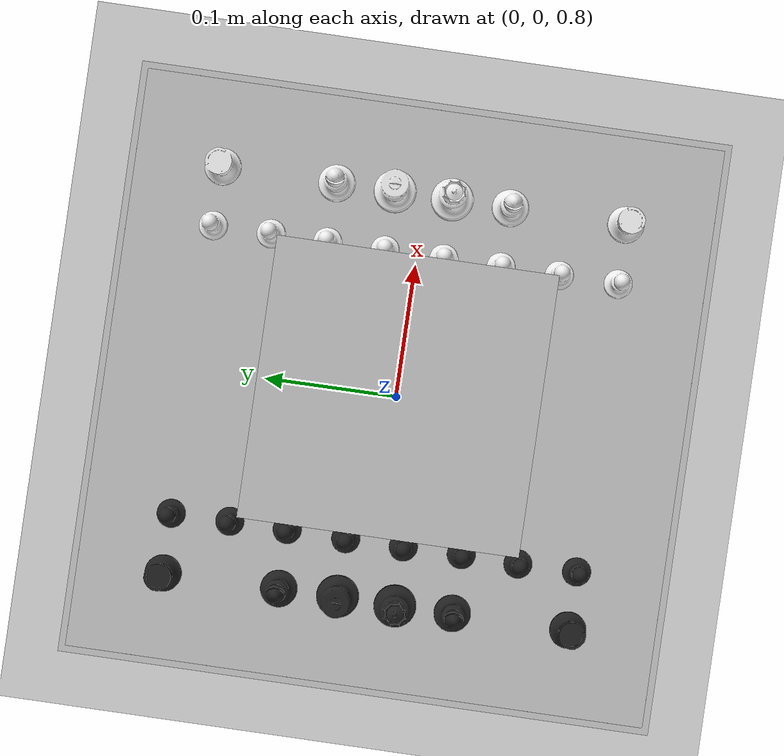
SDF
<sdf version="1.7">
 <world name="default">
  <light name="sun" type="directional">
   <pose>0 0 10 0 -0 0</pose>
   <diffuse>0.8 0.8 0.8 1</diffuse>
   <specular>0.2 0.2 0.2 1</specular>
   <attenuation>
    <range>1000</range>
    <constant>0.9</constant>
    <linear>0.01</linear>
    <quadratic>0.001</quadratic>
   </attenuation>
   <direction>-0.5 0.1 -0.9</direction>
   <spot><inner_angle>0</inner_angle><outer_angle>0</outer_angle><falloff>0</falloff></spot>
  </light>
  <model name="ground_plane">
   <static>1</static>
   <link name="link">
    <collision name="collision">
     <geometry><plane><normal>0 0 1</normal><size>100 100</size></plane></geometry>
     <surface>
      <contact><collide_bitmask>65535</collide_bitmask></contact>
      <friction><ode><mu>100</mu><mu2>50</mu2></ode></friction>
     </surface>
    </collision>
    <visual name="visual">
     <cast_shadows>0</cast_shadows>
     <geometry><plane><normal>0 0 1</normal><size>100 100</size></plane></geometry>
     <material>
      <script><uri>file://media/materials/scripts/gazebo.material</uri><name>Gazebo/Grey</name></script>
     </material>
    </visual>
   </link>
  </model>
  <gravity>0 0 -9.8</gravity>
  <magnetic_field>6e-06 2.3e-05 -4.2e-05</magnetic_field>
  <atmosphere type="adiabatic"/>
  <physics type="ode">
   <max_step_size>0.001</max_step_size>
   <real_time_factor>1</real_time_factor>
   <real_time_update_rate>1000</real_time_update_rate>
  </physics>
  <scene><ambient>0.4 0.4 0.4 1</ambient><background>0.7 0.7 0.7 1</background><shadows>1</shadows></scene>
  <spherical_coordinates>
   <surface_model>EARTH_WGS84</surface_model>
   <latitude_deg>0</latitude_deg>
   <longitude_deg>0</longitude_deg>
   <elevation>0</elevation>
   <heading_deg>0</heading_deg>
  </spherical_coordinates>
  <model name="chess_board">
   <link name="link">
    <inertial>
     <mass>0.5</mass>
     <inertia>
      <ixx>0.166667</ixx>
      <ixy>0</ixy>
      <ixz>0</ixz>
      <iyy>0.166667</iyy>
      <iyz>0</iyz>
      <izz>0.166667</izz>
     </inertia>
    </inertial>
    <visual name="visual">
     <geometry><box><size>0.44 0.44 0.02</size></box></geometry>
     <material>
      <script>
       <name>ChessBoardMaterial</name>
       <uri>model://chess_board/materials/scripts</uri>
       <uri>model://chess_board/materials/textures</uri>
      </script>
     </material>
    </visual>
    <collision name="collision">
     <geometry><box><size>0.44 0.44 0.02</size></box></geometry>
     <surface>
      <friction>
       <ode><mu>1</mu><mu2>1</mu2><fdir1>0 0 0</fdir1><slip1>0</slip1><slip2>0</slip2></ode>
       <torsional>
        <coefficient>1</coefficient>
        <patch_radius>0</patch_radius>
        <surface_radius>0</surface_radius>
        <use_patch_radius>1</use_patch_radius>
        <ode><slip>0</slip></ode>
       </torsional>
      </friction>
      <bounce><restitution_coefficient>0</restitution_coefficient><threshold>1e+06</threshold></bounce>
      <contact>
       <collide_without_contact>0</collide_without_contact>
       <collide_without_contact_bitmask>1</collide_without_contact_bitmask>
       <collide_bitmask>1</collide_bitmask>
       <ode>
        <soft_cfm>0</soft_cfm>
        <soft_erp>0.2</soft_erp>
        <kp>1e+13</kp>
        <kd>1</kd>
        <max_vel>0.01</max_vel>
        <min_depth>0</min_depth>
       </ode>
       <bullet>
        <split_impulse>1</split_impulse>
        <split_impulse_penetration_threshold>-0.01</split_impulse_penetration_threshold>
        <soft_cfm>0</soft_cfm>
        <soft_erp>0.2</soft_erp>
        <kp>1e+13</kp>
        <kd>1</kd>
       </bullet>
      </contact>
     </surface>
    </collision>
   </link>
   <static>0</static>
   <pose>-0.000715 0.00093 0.785 -0 -0 -3e-06</pose>
  </model>
  <model name="pawn_white">
   <link name="link">
    <inertial>
     <mass>0.1</mass>
     <inertia>
      <ixx>0.166667</ixx>
      <ixy>0</ixy>
      <ixz>0</ixz>
      <iyy>0.166667</iyy>
      <iyz>0</iyz>
      <izz>0.166667</izz>
     </inertia>
    </inertial>
    <visual name="visual">
     <geometry><mesh><uri>model://pawn_white/pawn.stl</uri><scale>0.001 0.001 0.001</scale></mesh></geometry>
     <material>
      <lighting>1</lighting>
      <script><uri>file://media/materials/scripts/gazebo.material</uri><name>Gazebo/White</name></script>
      <shader type="pixel"><normal_map>__default__</normal_map></shader>
      <ambient>1 1 1 1</ambient>
      <diffuse>1 1 1 1</diffuse>
      <specular>0.1 0.1 0.1 1</specular>
      <emissive>0 0 0 1</emissive>
     </material>
    </visual>
    <collision name="collision">
     <geometry><mesh><uri>model://pawn_white/pawn.stl</uri><scale>0.001 0.001 0.001</scale></mesh></geometry>
     <surface>
      <friction>
       <ode><mu>1</mu><mu2>1</mu2><fdir1>0 0 0</fdir1><slip1>0</slip1><slip2>0</slip2></ode>
       <torsional>
        <coefficient>1</coefficient>
        <patch_radius>0</patch_radius>
        <surface_radius>0</surface_radius>
        <use_patch_radius>1</use_patch_radius>
        <ode><slip>0</slip></ode>
       </torsional>
      </friction>
      <bounce><restitution_coefficient>0</restitution_coefficient><threshold>1e+06</threshold></bounce>
      <contact>
       <collide_without_contact>0</collide_without_contact>
       <collide_without_contact_bitmask>1</collide_without_contact_bitmask>
       <collide_bitmask>1</collide_bitmask>
       <ode>
        <soft_cfm>0</soft_cfm>
        <soft_erp>0.2</soft_erp>
        <kp>1e+13</kp>
        <kd>1</kd>
        <max_vel>0.01</max_vel>
        <min_depth>0</min_depth>
       </ode>
       <bullet>
        <split_impulse>1</split_impulse>
        <split_impulse_penetration_threshold>-0.01</split_impulse_penetration_threshold>
        <soft_cfm>0</soft_cfm>
        <soft_erp>0.2</soft_erp>
        <kp>1e+13</kp>
        <kd>1</kd>
       </bullet>
      </contact>
     </surface>
    </collision>
   </link>
   <static>0</static>
   <pose>0.108293 -0.153419 0.795226 -0.00037 -2.4e-05 0.004243</pose>
  </model>
  <model name="pawn_white_0">
   <link name="link">
    <inertial>
     <mass>0.1</mass>
     <inertia>
      <ixx>0.166667</ixx>
      <ixy>0</ixy>
      <ixz>0</ixz>
      <iyy>0.166667</iyy>
      <iyz>0</iyz>
      <izz>0.166667</izz>
     </inertia>
    </inertial>
    <visual name="visual">
     <geometry><mesh><uri>model://pawn_white/pawn.stl</uri><scale>0.001 0.001 0.001</scale></mesh></geometry>
     <material>
      <lighting>1</lighting>
      <script><uri>file://media/materials/scripts/gazebo.material</uri><name>Gazebo/White</name></script>
      <shader type="pixel"><normal_map>__default__</normal_map></shader>
      <ambient>1 1 1 1</ambient>
      <diffuse>1 1 1 1</diffuse>
      <specular>0.1 0.1 0.1 1</specular>
      <emissive>0 0 0 1</emissive>
     </material>
    </visual>
    <collision name="collision">
     <geometry><mesh><uri>model://pawn_white/pawn.stl</uri><scale>0.001 0.001 0.001</scale></mesh></geometry>
     <surface>
      <friction>
       <ode><mu>1</mu><mu2>1</mu2><fdir1>0 0 0</fdir1><slip1>0</slip1><slip2>0</slip2></ode>
       <torsional>
        <coefficient>1</coefficient>
        <patch_radius>0</patch_radius>
        <surface_radius>0</surface_radius>
        <use_patch_radius>1</use_patch_radius>
        <ode><slip>0</slip></ode>
       </torsional>
      </friction>
      <bounce><restitution_coefficient>0</restitution_coefficient><threshold>1e+06</threshold></bounce>
      <contact>
       <collide_without_contact>0</collide_without_contact>
       <collide_without_contact_bitmask>1</collide_without_contact_bitmask>
       <collide_bitmask>1</collide_bitmask>
       <ode>
        <soft_cfm>0</soft_cfm>
        <soft_erp>0.2</soft_erp>
        <kp>1e+13</kp>
        <kd>1</kd>
        <max_vel>0.01</max_vel>
        <min_depth>0</min_depth>
       </ode>
       <bullet>
        <split_impulse>1</split_impulse>
        <split_impulse_penetration_threshold>-0.01</split_impulse_penetration_threshold>
        <soft_cfm>0</soft_cfm>
        <soft_erp>0.2</soft_erp>
        <kp>1e+13</kp>
        <kd>1</kd>
       </bullet>
      </contact>
     </surface>
    </collision>
   </link>
   <static>0</static>
   <pose>0.10847 -0.108572 0.795231 0.000772 -2.1e-05 0.008904</pose>
  </model>
  <model name="pawn_white_1">
   <link name="link">
    <inertial>
     <mass>0.1</mass>
     <inertia>
      <ixx>0.166667</ixx>
      <ixy>0</ixy>
      <ixz>0</ixz>
      <iyy>0.166667</iyy>
      <iyz>0</iyz>
      <izz>0.166667</izz>
     </inertia>
    </inertial>
    <visual name="visual">
     <geometry><mesh><uri>model://pawn_white/pawn.stl</uri><scale>0.001 0.001 0.001</scale></mesh></geometry>
     <material>
      <lighting>1</lighting>
      <script><uri>file://media/materials/scripts/gazebo.material</uri><name>Gazebo/White</name></script>
      <shader type="pixel"><normal_map>__default__</normal_map></shader>
      <ambient>1 1 1 1</ambient>
      <diffuse>1 1 1 1</diffuse>
      <specular>0.1 0.1 0.1 1</specular>
      <emissive>0 0 0 1</emissive>
     </material>
    </visual>
    <collision name="collision">
     <geometry><mesh><uri>model://pawn_white/pawn.stl</uri><scale>0.001 0.001 0.001</scale></mesh></geometry>
     <surface>
      <friction>
       <ode><mu>1</mu><mu2>1</mu2><fdir1>0 0 0</fdir1><slip1>0</slip1><slip2>0</slip2></ode>
       <torsional>
        <coefficient>1</coefficient>
        <patch_radius>0</patch_radius>
        <surface_radius>0</surface_radius>
        <use_patch_radius>1</use_patch_radius>
        <ode><slip>0</slip></ode>
       </torsional>
      </friction>
      <bounce><restitution_coefficient>0</restitution_coefficient><threshold>1e+06</threshold></bounce>
      <contact>
       <collide_without_contact>0</collide_without_contact>
       <collide_without_contact_bitmask>1</collide_without_contact_bitmask>
       <collide_bitmask>1</collide_bitmask>
       <ode>
        <soft_cfm>0</soft_cfm>
        <soft_erp>0.2</soft_erp>
        <kp>1e+13</kp>
        <kd>1</kd>
        <max_vel>0.01</max_vel>
        <min_depth>0</min_depth>
       </ode>
       <bullet>
        <split_impulse>1</split_impulse>
        <split_impulse_penetration_threshold>-0.01</split_impulse_penetration_threshold>
        <soft_cfm>0</soft_cfm>
        <soft_erp>0.2</soft_erp>
        <kp>1e+13</kp>
        <kd>1</kd>
       </bullet>
      </contact>
     </surface>
    </collision>
   </link>
   <static>0</static>
   <pose>0.108512 -0.064083 0.795224 0.000133 2.1e-05 0.023056</pose>
  </model>
  <model name="pawn_white_2">
   <link name="link">
    <inertial>
     <mass>0.1</mass>
     <inertia>
      <ixx>0.166667</ixx>
      <ixy>0</ixy>
      <ixz>0</ixz>
      <iyy>0.166667</iyy>
      <iyz>0</iyz>
      <izz>0.166667</izz>
     </inertia>
    </inertial>
    <visual name="visual">
     <geometry><mesh><uri>model://pawn_white/pawn.stl</uri><scale>0.001 0.001 0.001</scale></mesh></geometry>
     <material>
      <lighting>1</lighting>
      <script><uri>file://media/materials/scripts/gazebo.material</uri><name>Gazebo/White</name></script>
      <shader type="pixel"><normal_map>__default__</normal_map></shader>
      <ambient>1 1 1 1</ambient>
      <diffuse>1 1 1 1</diffuse>
      <specular>0.1 0.1 0.1 1</specular>
      <emissive>0 0 0 1</emissive>
     </material>
    </visual>
    <collision name="collision">
     <geometry><mesh><uri>model://pawn_white/pawn.stl</uri><scale>0.001 0.001 0.001</scale></mesh></geometry>
     <surface>
      <friction>
       <ode><mu>1</mu><mu2>1</mu2><fdir1>0 0 0</fdir1><slip1>0</slip1><slip2>0</slip2></ode>
       <torsional>
        <coefficient>1</coefficient>
        <patch_radius>0</patch_radius>
        <surface_radius>0</surface_radius>
        <use_patch_radius>1</use_patch_radius>
        <ode><slip>0</slip></ode>
       </torsional>
      </friction>
      <bounce><restitution_coefficient>0</restitution_coefficient><threshold>1e+06</threshold></bounce>
      <contact>
       <collide_without_contact>0</collide_without_contact>
       <collide_without_contact_bitmask>1</collide_without_contact_bitmask>
       <collide_bitmask>1</collide_bitmask>
       <ode>
        <soft_cfm>0</soft_cfm>
        <soft_erp>0.2</soft_erp>
        <kp>1e+13</kp>
        <kd>1</kd>
        <max_vel>0.01</max_vel>
        <min_depth>0</min_depth>
       </ode>
       <bullet>
        <split_impulse>1</split_impulse>
        <split_impulse_penetration_threshold>-0.01</split_impulse_penetration_threshold>
        <soft_cfm>0</soft_cfm>
        <soft_erp>0.2</soft_erp>
        <kp>1e+13</kp>
        <kd>1</kd>
       </bullet>
      </contact>
     </surface>
    </collision>
   </link>
   <static>0</static>
   <pose>0.108532 -0.020463 0.795231 -0.000812 0.000112 0.013914</pose>
  </model>
  <model name="pawn_white_3">
   <link name="link">
    <inertial>
     <mass>0.1</mass>
     <inertia>
      <ixx>0.166667</ixx>
      <ixy>0</ixy>
      <ixz>0</ixz>
      <iyy>0.166667</iyy>
      <iyz>0</iyz>
      <izz>0.166667</izz>
     </inertia>
    </inertial>
    <visual name="visual">
     <geometry><mesh><uri>model://pawn_white/pawn.stl</uri><scale>0.001 0.001 0.001</scale></mesh></geometry>
     <material>
      <lighting>1</lighting>
      <script><uri>file://media/materials/scripts/gazebo.material</uri><name>Gazebo/White</name></script>
      <shader type="pixel"><normal_map>__default__</normal_map></shader>
      <ambient>1 1 1 1</ambient>
      <diffuse>1 1 1 1</diffuse>
      <specular>0.1 0.1 0.1 1</specular>
      <emissive>0 0 0 1</emissive>
     </material>
    </visual>
    <collision name="collision">
     <geometry><mesh><uri>model://pawn_white/pawn.stl</uri><scale>0.001 0.001 0.001</scale></mesh></geometry>
     <surface>
      <friction>
       <ode><mu>1</mu><mu2>1</mu2><fdir1>0 0 0</fdir1><slip1>0</slip1><slip2>0</slip2></ode>
       <torsional>
        <coefficient>1</coefficient>
        <patch_radius>0</patch_radius>
        <surface_radius>0</surface_radius>
        <use_patch_radius>1</use_patch_radius>
        <ode><slip>0</slip></ode>
       </torsional>
      </friction>
      <bounce><restitution_coefficient>0</restitution_coefficient><threshold>1e+06</threshold></bounce>
      <contact>
       <collide_without_contact>0</collide_without_contact>
       <collide_without_contact_bitmask>1</collide_without_contact_bitmask>
       <collide_bitmask>1</collide_bitmask>
       <ode>
        <soft_cfm>0</soft_cfm>
        <soft_erp>0.2</soft_erp>
        <kp>1e+13</kp>
        <kd>1</kd>
        <max_vel>0.01</max_vel>
        <min_depth>0</min_depth>
       </ode>
       <bullet>
        <split_impulse>1</split_impulse>
        <split_impulse_penetration_threshold>-0.01</split_impulse_penetration_threshold>
        <soft_cfm>0</soft_cfm>
        <soft_erp>0.2</soft_erp>
        <kp>1e+13</kp>
        <kd>1</kd>
       </bullet>
      </contact>
     </surface>
    </collision>
   </link>
   <static>0</static>
   <pose>0.108569 0.024248 0.795231 0.000532 -0.000583 0.00706</pose>
  </model>
  <model name="pawn_white_4">
   <link name="link">
    <inertial>
     <mass>0.1</mass>
     <inertia>
      <ixx>0.166667</ixx>
      <ixy>0</ixy>
      <ixz>0</ixz>
      <iyy>0.166667</iyy>
      <iyz>0</iyz>
      <izz>0.166667</izz>
     </inertia>
    </inertial>
    <visual name="visual">
     <geometry><mesh><uri>model://pawn_white/pawn.stl</uri><scale>0.001 0.001 0.001</scale></mesh></geometry>
     <material>
      <lighting>1</lighting>
      <script><uri>file://media/materials/scripts/gazebo.material</uri><name>Gazebo/White</name></script>
      <shader type="pixel"><normal_map>__default__</normal_map></shader>
      <ambient>1 1 1 1</ambient>
      <diffuse>1 1 1 1</diffuse>
      <specular>0.1 0.1 0.1 1</specular>
      <emissive>0 0 0 1</emissive>
     </material>
    </visual>
    <collision name="collision">
     <geometry><mesh><uri>model://pawn_white/pawn.stl</uri><scale>0.001 0.001 0.001</scale></mesh></geometry>
     <surface>
      <friction>
       <ode><mu>1</mu><mu2>1</mu2><fdir1>0 0 0</fdir1><slip1>0</slip1><slip2>0</slip2></ode>
       <torsional>
        <coefficient>1</coefficient>
        <patch_radius>0</patch_radius>
        <surface_radius>0</surface_radius>
        <use_patch_radius>1</use_patch_radius>
        <ode><slip>0</slip></ode>
       </torsional>
      </friction>
      <bounce><restitution_coefficient>0</restitution_coefficient><threshold>1e+06</threshold></bounce>
      <contact>
       <collide_without_contact>0</collide_without_contact>
       <collide_without_contact_bitmask>1</collide_without_contact_bitmask>
       <collide_bitmask>1</collide_bitmask>
       <ode>
        <soft_cfm>0</soft_cfm>
        <soft_erp>0.2</soft_erp>
        <kp>1e+13</kp>
        <kd>1</kd>
        <max_vel>0.01</max_vel>
        <min_depth>0</min_depth>
       </ode>
       <bullet>
        <split_impulse>1</split_impulse>
        <split_impulse_penetration_threshold>-0.01</split_impulse_penetration_threshold>
        <soft_cfm>0</soft_cfm>
        <soft_erp>0.2</soft_erp>
        <kp>1e+13</kp>
        <kd>1</kd>
       </bullet>
      </contact>
     </surface>
    </collision>
   </link>
   <static>0</static>
   <pose>0.108574 0.068031 0.795226 0.000129 -0.000297 0.000487</pose>
  </model>
  <model name="pawn_white_5">
   <link name="link">
    <inertial>
     <mass>0.1</mass>
     <inertia>
      <ixx>0.166667</ixx>
      <ixy>0</ixy>
      <ixz>0</ixz>
      <iyy>0.166667</iyy>
      <iyz>0</iyz>
      <izz>0.166667</izz>
     </inertia>
    </inertial>
    <visual name="visual">
     <geometry><mesh><uri>model://pawn_white/pawn.stl</uri><scale>0.001 0.001 0.001</scale></mesh></geometry>
     <material>
      <lighting>1</lighting>
      <script><uri>file://media/materials/scripts/gazebo.material</uri><name>Gazebo/White</name></script>
      <shader type="pixel"><normal_map>__default__</normal_map></shader>
      <ambient>1 1 1 1</ambient>
      <diffuse>1 1 1 1</diffuse>
      <specular>0.1 0.1 0.1 1</specular>
      <emissive>0 0 0 1</emissive>
     </material>
    </visual>
    <collision name="collision">
     <geometry><mesh><uri>model://pawn_white/pawn.stl</uri><scale>0.001 0.001 0.001</scale></mesh></geometry>
     <surface>
      <friction>
       <ode><mu>1</mu><mu2>1</mu2><fdir1>0 0 0</fdir1><slip1>0</slip1><slip2>0</slip2></ode>
       <torsional>
        <coefficient>1</coefficient>
        <patch_radius>0</patch_radius>
        <surface_radius>0</surface_radius>
        <use_patch_radius>1</use_patch_radius>
        <ode><slip>0</slip></ode>
       </torsional>
      </friction>
      <bounce><restitution_coefficient>0</restitution_coefficient><threshold>1e+06</threshold></bounce>
      <contact>
       <collide_without_contact>0</collide_without_contact>
       <collide_without_contact_bitmask>1</collide_without_contact_bitmask>
       <collide_bitmask>1</collide_bitmask>
       <ode>
        <soft_cfm>0</soft_cfm>
        <soft_erp>0.2</soft_erp>
        <kp>1e+13</kp>
        <kd>1</kd>
        <max_vel>0.01</max_vel>
        <min_depth>0</min_depth>
       </ode>
       <bullet>
        <split_impulse>1</split_impulse>
        <split_impulse_penetration_threshold>-0.01</split_impulse_penetration_threshold>
        <soft_cfm>0</soft_cfm>
        <soft_erp>0.2</soft_erp>
        <kp>1e+13</kp>
        <kd>1</kd>
       </bullet>
      </contact>
     </surface>
    </collision>
   </link>
   <static>0</static>
   <pose>0.108693 0.111114 0.795187 -0.000192 -0.000199 -0.010673</pose>
  </model>
  <model name="pawn_white_6">
   <link name="link">
    <inertial>
     <mass>0.1</mass>
     <inertia>
      <ixx>0.166667</ixx>
      <ixy>0</ixy>
      <ixz>0</ixz>
      <iyy>0.166667</iyy>
      <iyz>0</iyz>
      <izz>0.166667</izz>
     </inertia>
    </inertial>
    <visual name="visual">
     <geometry><mesh><uri>model://pawn_white/pawn.stl</uri><scale>0.001 0.001 0.001</scale></mesh></geometry>
     <material>
      <lighting>1</lighting>
      <script><uri>file://media/materials/scripts/gazebo.material</uri><name>Gazebo/White</name></script>
      <shader type="pixel"><normal_map>__default__</normal_map></shader>
      <ambient>1 1 1 1</ambient>
      <diffuse>1 1 1 1</diffuse>
      <specular>0.1 0.1 0.1 1</specular>
      <emissive>0 0 0 1</emissive>
     </material>
    </visual>
    <collision name="collision">
     <geometry><mesh><uri>model://pawn_white/pawn.stl</uri><scale>0.001 0.001 0.001</scale></mesh></geometry>
     <surface>
      <friction>
       <ode><mu>1</mu><mu2>1</mu2><fdir1>0 0 0</fdir1><slip1>0</slip1><slip2>0</slip2></ode>
       <torsional>
        <coefficient>1</coefficient>
        <patch_radius>0</patch_radius>
        <surface_radius>0</surface_radius>
        <use_patch_radius>1</use_patch_radius>
        <ode><slip>0</slip></ode>
       </torsional>
      </friction>
      <bounce><restitution_coefficient>0</restitution_coefficient><threshold>1e+06</threshold></bounce>
      <contact>
       <collide_without_contact>0</collide_without_contact>
       <collide_without_contact_bitmask>1</collide_without_contact_bitmask>
       <collide_bitmask>1</collide_bitmask>
       <ode>
        <soft_cfm>0</soft_cfm>
        <soft_erp>0.2</soft_erp>
        <kp>1e+13</kp>
        <kd>1</kd>
        <max_vel>0.01</max_vel>
        <min_depth>0</min_depth>
       </ode>
       <bullet>
        <split_impulse>1</split_impulse>
        <split_impulse_penetration_threshold>-0.01</split_impulse_penetration_threshold>
        <soft_cfm>0</soft_cfm>
        <soft_erp>0.2</soft_erp>
        <kp>1e+13</kp>
        <kd>1</kd>
       </bullet>
      </contact>
     </surface>
    </collision>
   </link>
   <static>0</static>
   <pose>0.108595 0.155192 0.795232 0.000167 -0.000938 -0.018302</pose>
  </model>
  <model name="rook_white">
   <link name="link">
    <inertial>
     <mass>0.1</mass>
     <inertia>
      <ixx>0.166667</ixx>
      <ixy>0</ixy>
      <ixz>0</ixz>
      <iyy>0.166667</iyy>
      <iyz>0</iyz>
      <izz>0.166667</izz>
     </inertia>
    </inertial>
    <visual name="visual">
     <geometry><mesh><uri>model://rook_white/rook.stl</uri><scale>0.001 0.001 0.001</scale></mesh></geometry>
     <material>
      <lighting>1</lighting>
      <script><uri>file://media/materials/scripts/gazebo.material</uri><name>Gazebo/White</name></script>
      <shader type="pixel"><normal_map>__default__</normal_map></shader>
      <ambient>1 1 1 1</ambient>
      <diffuse>1 1 1 1</diffuse>
      <specular>0.1 0.1 0.1 1</specular>
      <emissive>0 0 0 1</emissive>
     </material>
    </visual>
    <collision name="collision">
     <geometry><mesh><uri>model://rook_white/rook.stl</uri><scale>0.001 0.001 0.001</scale></mesh></geometry>
     <surface>
      <friction>
       <ode><mu>1</mu><mu2>1</mu2><fdir1>0 0 0</fdir1><slip1>0</slip1><slip2>0</slip2></ode>
       <torsional>
        <coefficient>1</coefficient>
        <patch_radius>0</patch_radius>
        <surface_radius>0</surface_radius>
        <use_patch_radius>1</use_patch_radius>
        <ode><slip>0</slip></ode>
       </torsional>
      </friction>
      <bounce><restitution_coefficient>0</restitution_coefficient><threshold>1e+06</threshold></bounce>
      <contact>
       <collide_without_contact>0</collide_without_contact>
       <collide_without_contact_bitmask>1</collide_without_contact_bitmask>
       <collide_bitmask>1</collide_bitmask>
       <ode>
        <soft_cfm>0</soft_cfm>
        <soft_erp>0.2</soft_erp>
        <kp>1e+13</kp>
        <kd>1</kd>
        <max_vel>0.01</max_vel>
        <min_depth>0</min_depth>
       </ode>
       <bullet>
        <split_impulse>1</split_impulse>
        <split_impulse_penetration_threshold>-0.01</split_impulse_penetration_threshold>
        <soft_cfm>0</soft_cfm>
        <soft_erp>0.2</soft_erp>
        <kp>1e+13</kp>
        <kd>1</kd>
       </bullet>
      </contact>
     </surface>
    </collision>
   </link>
   <static>0</static>
   <pose>0.153377 -0.152852 0.795175 8.5e-05 -0.000113 0.003346</pose>
  </model>
  <model name="rook_white_0">
   <link name="link">
    <inertial>
     <mass>0.1</mass>
     <inertia>
      <ixx>0.166667</ixx>
      <ixy>0</ixy>
      <ixz>0</ixz>
      <iyy>0.166667</iyy>
      <iyz>0</iyz>
      <izz>0.166667</izz>
     </inertia>
    </inertial>
    <visual name="visual">
     <geometry><mesh><uri>model://rook_white/rook.stl</uri><scale>0.001 0.001 0.001</scale></mesh></geometry>
     <material>
      <lighting>1</lighting>
      <script><uri>file://media/materials/scripts/gazebo.material</uri><name>Gazebo/White</name></script>
      <shader type="pixel"><normal_map>__default__</normal_map></shader>
      <ambient>1 1 1 1</ambient>
      <diffuse>1 1 1 1</diffuse>
      <specular>0.1 0.1 0.1 1</specular>
      <emissive>0 0 0 1</emissive>
     </material>
    </visual>
    <collision name="collision">
     <geometry><mesh><uri>model://rook_white/rook.stl</uri><scale>0.001 0.001 0.001</scale></mesh></geometry>
     <surface>
      <friction>
       <ode><mu>1</mu><mu2>1</mu2><fdir1>0 0 0</fdir1><slip1>0</slip1><slip2>0</slip2></ode>
       <torsional>
        <coefficient>1</coefficient>
        <patch_radius>0</patch_radius>
        <surface_radius>0</surface_radius>
        <use_patch_radius>1</use_patch_radius>
        <ode><slip>0</slip></ode>
       </torsional>
      </friction>
      <bounce><restitution_coefficient>0</restitution_coefficient><threshold>1e+06</threshold></bounce>
      <contact>
       <collide_without_contact>0</collide_without_contact>
       <collide_without_contact_bitmask>1</collide_without_contact_bitmask>
       <collide_bitmask>1</collide_bitmask>
       <ode>
        <soft_cfm>0</soft_cfm>
        <soft_erp>0.2</soft_erp>
        <kp>1e+13</kp>
        <kd>1</kd>
        <max_vel>0.01</max_vel>
        <min_depth>0</min_depth>
       </ode>
       <bullet>
        <split_impulse>1</split_impulse>
        <split_impulse_penetration_threshold>-0.01</split_impulse_penetration_threshold>
        <soft_cfm>0</soft_cfm>
        <soft_erp>0.2</soft_erp>
        <kp>1e+13</kp>
        <kd>1</kd>
       </bullet>
      </contact>
     </surface>
    </collision>
   </link>
   <static>0</static>
   <pose>0.153431 0.154267 0.795135 8e-06 -1.6e-05 -0.011572</pose>
  </model>
  <model name="bishop_white">
   <link name="link">
    <inertial>
     <mass>0.1</mass>
     <inertia>
      <ixx>0.166667</ixx>
      <ixy>0</ixy>
      <ixz>0</ixz>
      <iyy>0.166667</iyy>
      <iyz>0</iyz>
      <izz>0.166667</izz>
     </inertia>
    </inertial>
    <visual name="visual">
     <geometry><mesh><uri>model://bishop_white/bishop.stl</uri><scale>0.001 0.001 0.001</scale></mesh></geometry>
     <material>
      <lighting>1</lighting>
      <script><uri>file://media/materials/scripts/gazebo.material</uri><name>Gazebo/White</name></script>
      <shader type="pixel"><normal_map>__default__</normal_map></shader>
      <ambient>1 1 1 1</ambient>
      <diffuse>1 1 1 1</diffuse>
      <specular>0.1 0.1 0.1 1</specular>
      <emissive>0 0 0 1</emissive>
     </material>
    </visual>
    <collision name="collision">
     <geometry><mesh><uri>model://bishop_white/bishop.stl</uri><scale>0.001 0.001 0.001</scale></mesh></geometry>
     <surface>
      <friction>
       <ode><mu>1</mu><mu2>1</mu2><fdir1>0 0 0</fdir1><slip1>0</slip1><slip2>0</slip2></ode>
       <torsional>
        <coefficient>1</coefficient>
        <patch_radius>0</patch_radius>
        <surface_radius>0</surface_radius>
        <use_patch_radius>1</use_patch_radius>
        <ode><slip>0</slip></ode>
       </torsional>
      </friction>
      <bounce><restitution_coefficient>0</restitution_coefficient><threshold>1e+06</threshold></bounce>
      <contact>
       <collide_without_contact>0</collide_without_contact>
       <collide_without_contact_bitmask>1</collide_without_contact_bitmask>
       <collide_bitmask>1</collide_bitmask>
       <ode>
        <soft_cfm>0</soft_cfm>
        <soft_erp>0.2</soft_erp>
        <kp>1e+13</kp>
        <kd>1</kd>
        <max_vel>0.01</max_vel>
        <min_depth>0</min_depth>
       </ode>
       <bullet>
        <split_impulse>1</split_impulse>
        <split_impulse_penetration_threshold>-0.01</split_impulse_penetration_threshold>
        <soft_cfm>0</soft_cfm>
        <soft_erp>0.2</soft_erp>
        <kp>1e+13</kp>
        <kd>1</kd>
       </bullet>
      </contact>
     </surface>
    </collision>
   </link>
   <static>0</static>
   <pose>0.153448 -0.064865 0.795056 0.000145 -0.000137 0.003791</pose>
  </model>
  <model name="bishop_white_0">
   <link name="link">
    <inertial>
     <mass>0.1</mass>
     <inertia>
      <ixx>0.166667</ixx>
      <ixy>0</ixy>
      <ixz>0</ixz>
      <iyy>0.166667</iyy>
      <iyz>0</iyz>
      <izz>0.166667</izz>
     </inertia>
    </inertial>
    <visual name="visual">
     <geometry><mesh><uri>model://bishop_white/bishop.stl</uri><scale>0.001 0.001 0.001</scale></mesh></geometry>
     <material>
      <lighting>1</lighting>
      <script><uri>file://media/materials/scripts/gazebo.material</uri><name>Gazebo/White</name></script>
      <shader type="pixel"><normal_map>__default__</normal_map></shader>
      <ambient>1 1 1 1</ambient>
      <diffuse>1 1 1 1</diffuse>
      <specular>0.1 0.1 0.1 1</specular>
      <emissive>0 0 0 1</emissive>
     </material>
    </visual>
    <collision name="collision">
     <geometry><mesh><uri>model://bishop_white/bishop.stl</uri><scale>0.001 0.001 0.001</scale></mesh></geometry>
     <surface>
      <friction>
       <ode><mu>1</mu><mu2>1</mu2><fdir1>0 0 0</fdir1><slip1>0</slip1><slip2>0</slip2></ode>
       <torsional>
        <coefficient>1</coefficient>
        <patch_radius>0</patch_radius>
        <surface_radius>0</surface_radius>
        <use_patch_radius>1</use_patch_radius>
        <ode><slip>0</slip></ode>
       </torsional>
      </friction>
      <bounce><restitution_coefficient>0</restitution_coefficient><threshold>1e+06</threshold></bounce>
      <contact>
       <collide_without_contact>0</collide_without_contact>
       <collide_without_contact_bitmask>1</collide_without_contact_bitmask>
       <collide_bitmask>1</collide_bitmask>
       <ode>
        <soft_cfm>0</soft_cfm>
        <soft_erp>0.2</soft_erp>
        <kp>1e+13</kp>
        <kd>1</kd>
        <max_vel>0.01</max_vel>
        <min_depth>0</min_depth>
       </ode>
       <bullet>
        <split_impulse>1</split_impulse>
        <split_impulse_penetration_threshold>-0.01</split_impulse_penetration_threshold>
        <soft_cfm>0</soft_cfm>
        <soft_erp>0.2</soft_erp>
        <kp>1e+13</kp>
        <kd>1</kd>
       </bullet>
      </contact>
     </surface>
    </collision>
   </link>
   <static>0</static>
   <pose>0.153381 0.067428 0.795079 2.6e-05 -2.6e-05 -0.008082</pose>
  </model>
  <model name="queen_white">
   <link name="link">
    <inertial>
     <mass>0.1</mass>
     <inertia>
      <ixx>0.166667</ixx>
      <ixy>0</ixy>
      <ixz>0</ixz>
      <iyy>0.166667</iyy>
      <iyz>0</iyz>
      <izz>0.166667</izz>
     </inertia>
    </inertial>
    <visual name="visual">
     <geometry><mesh><uri>model://queen_white/queen.stl</uri><scale>0.001 0.001 0.001</scale></mesh></geometry>
     <material>
      <lighting>1</lighting>
      <script><uri>file://media/materials/scripts/gazebo.material</uri><name>Gazebo/White</name></script>
      <shader type="pixel"><normal_map>__default__</normal_map></shader>
      <ambient>1 1 1 1</ambient>
      <diffuse>1 1 1 1</diffuse>
      <specular>0.1 0.1 0.1 1</specular>
      <emissive>0 0 0 1</emissive>
     </material>
    </visual>
    <collision name="collision">
     <geometry><mesh><uri>model://queen_white/queen.stl</uri><scale>0.001 0.001 0.001</scale></mesh></geometry>
     <surface>
      <friction>
       <ode><mu>1</mu><mu2>1</mu2><fdir1>0 0 0</fdir1><slip1>0</slip1><slip2>0</slip2></ode>
       <torsional>
        <coefficient>1</coefficient>
        <patch_radius>0</patch_radius>
        <surface_radius>0</surface_radius>
        <use_patch_radius>1</use_patch_radius>
        <ode><slip>0</slip></ode>
       </torsional>
      </friction>
      <bounce><restitution_coefficient>0</restitution_coefficient><threshold>1e+06</threshold></bounce>
      <contact>
       <collide_without_contact>0</collide_without_contact>
       <collide_without_contact_bitmask>1</collide_without_contact_bitmask>
       <collide_bitmask>1</collide_bitmask>
       <ode>
        <soft_cfm>0</soft_cfm>
        <soft_erp>0.2</soft_erp>
        <kp>1e+13</kp>
        <kd>1</kd>
        <max_vel>0.01</max_vel>
        <min_depth>0</min_depth>
       </ode>
       <bullet>
        <split_impulse>1</split_impulse>
        <split_impulse_penetration_threshold>-0.01</split_impulse_penetration_threshold>
        <soft_cfm>0</soft_cfm>
        <soft_erp>0.2</soft_erp>
        <kp>1e+13</kp>
        <kd>1</kd>
       </bullet>
      </contact>
     </surface>
    </collision>
   </link>
   <static>0</static>
   <pose>0.153456 -0.020495 0.794905 1.2e-05 -2.1e-05 -0.002225</pose>
  </model>
  <model name="king_white">
   <link name="link">
    <inertial>
     <mass>0.1</mass>
     <inertia>
      <ixx>0.166667</ixx>
      <ixy>0</ixy>
      <ixz>0</ixz>
      <iyy>0.166667</iyy>
      <iyz>0</iyz>
      <izz>0.166667</izz>
     </inertia>
    </inertial>
    <visual name="visual">
     <geometry><mesh><uri>model://king_white/king.stl</uri><scale>0.001 0.001 0.001</scale></mesh></geometry>
     <material>
      <lighting>1</lighting>
      <script><uri>file://media/materials/scripts/gazebo.material</uri><name>Gazebo/White</name></script>
      <shader type="pixel"><normal_map>__default__</normal_map></shader>
      <ambient>1 1 1 1</ambient>
      <diffuse>1 1 1 1</diffuse>
      <specular>0.1 0.1 0.1 1</specular>
      <emissive>0 0 0 1</emissive>
     </material>
    </visual>
    <collision name="collision">
     <geometry><mesh><uri>model://king_white/king.stl</uri><scale>0.001 0.001 0.001</scale></mesh></geometry>
     <surface>
      <friction>
       <ode><mu>1</mu><mu2>1</mu2><fdir1>0 0 0</fdir1><slip1>0</slip1><slip2>0</slip2></ode>
       <torsional>
        <coefficient>1</coefficient>
        <patch_radius>0</patch_radius>
        <surface_radius>0</surface_radius>
        <use_patch_radius>1</use_patch_radius>
        <ode><slip>0</slip></ode>
       </torsional>
      </friction>
      <bounce><restitution_coefficient>0</restitution_coefficient><threshold>1e+06</threshold></bounce>
      <contact>
       <collide_without_contact>0</collide_without_contact>
       <collide_without_contact_bitmask>1</collide_without_contact_bitmask>
       <collide_bitmask>1</collide_bitmask>
       <ode>
        <soft_cfm>0</soft_cfm>
        <soft_erp>0.2</soft_erp>
        <kp>1e+13</kp>
        <kd>1</kd>
        <max_vel>0.01</max_vel>
        <min_depth>0</min_depth>
       </ode>
       <bullet>
        <split_impulse>1</split_impulse>
        <split_impulse_penetration_threshold>-0.01</split_impulse_penetration_threshold>
        <soft_cfm>0</soft_cfm>
        <soft_erp>0.2</soft_erp>
        <kp>1e+13</kp>
        <kd>1</kd>
       </bullet>
      </contact>
     </surface>
    </collision>
   </link>
   <static>0</static>
   <pose>0.15349 0.023065 0.7947 -1.4e-05 -1.2e-05 1.57236</pose>
  </model>
  <model name="pawn_black">
   <link name="link">
    <inertial>
     <mass>0.1</mass>
     <inertia>
      <ixx>0.166667</ixx>
      <ixy>0</ixy>
      <ixz>0</ixz>
      <iyy>0.166667</iyy>
      <iyz>0</iyz>
      <izz>0.166667</izz>
     </inertia>
    </inertial>
    <visual name="visual">
     <geometry><mesh><uri>model://pawn_black/pawn.stl</uri><scale>0.001 0.001 0.001</scale></mesh></geometry>
     <material>
      <lighting>1</lighting>
      <script><uri>file://media/materials/scripts/gazebo.material</uri><name>Gazebo/Black</name></script>
      <shader type="pixel"><normal_map>__default__</normal_map></shader>
      <ambient>0.3 0.3 0.3 1</ambient>
      <diffuse>0.3 0.3 0.3 1</diffuse>
      <specular>0.1 0.1 0.1 1</specular>
      <emissive>0 0 0 1</emissive>
     </material>
    </visual>
    <collision name="collision">
     <geometry><mesh><uri>model://pawn_black/pawn.stl</uri><scale>0.001 0.001 0.001</scale></mesh></geometry>
     <surface>
      <friction>
       <ode><mu>1</mu><mu2>1</mu2><fdir1>0 0 0</fdir1><slip1>0</slip1><slip2>0</slip2></ode>
       <torsional>
        <coefficient>1</coefficient>
        <patch_radius>0</patch_radius>
        <surface_radius>0</surface_radius>
        <use_patch_radius>1</use_patch_radius>
        <ode><slip>0</slip></ode>
       </torsional>
      </friction>
      <bounce><restitution_coefficient>0</restitution_coefficient><threshold>1e+06</threshold></bounce>
      <contact>
       <collide_without_contact>0</collide_without_contact>
       <collide_without_contact_bitmask>1</collide_without_contact_bitmask>
       <collide_bitmask>1</collide_bitmask>
       <ode>
        <soft_cfm>0</soft_cfm>
        <soft_erp>0.2</soft_erp>
        <kp>1e+13</kp>
        <kd>1</kd>
        <max_vel>0.01</max_vel>
        <min_depth>0</min_depth>
       </ode>
       <bullet>
        <split_impulse>1</split_impulse>
        <split_impulse_penetration_threshold>-0.01</split_impulse_penetration_threshold>
        <soft_cfm>0</soft_cfm>
        <soft_erp>0.2</soft_erp>
        <kp>1e+13</kp>
        <kd>1</kd>
       </bullet>
      </contact>
     </surface>
    </collision>
   </link>
   <static>0</static>
   <pose>-0.111047 -0.153394 0.795229 0.000326 -0.000526 0.002873</pose>
  </model>
  <model name="pawn_black_0">
   <link name="link">
    <inertial>
     <mass>0.1</mass>
     <inertia>
      <ixx>0.166667</ixx>
      <ixy>0</ixy>
      <ixz>0</ixz>
      <iyy>0.166667</iyy>
      <iyz>0</iyz>
      <izz>0.166667</izz>
     </inertia>
    </inertial>
    <visual name="visual">
     <geometry><mesh><uri>model://pawn_black/pawn.stl</uri><scale>0.001 0.001 0.001</scale></mesh></geometry>
     <material>
      <lighting>1</lighting>
      <script><uri>file://media/materials/scripts/gazebo.material</uri><name>Gazebo/Black</name></script>
      <shader type="pixel"><normal_map>__default__</normal_map></shader>
      <ambient>0.3 0.3 0.3 1</ambient>
      <diffuse>0.3 0.3 0.3 1</diffuse>
      <specular>0.1 0.1 0.1 1</specular>
      <emissive>0 0 0 1</emissive>
     </material>
    </visual>
    <collision name="collision">
     <geometry><mesh><uri>model://pawn_black/pawn.stl</uri><scale>0.001 0.001 0.001</scale></mesh></geometry>
     <surface>
      <friction>
       <ode><mu>1</mu><mu2>1</mu2><fdir1>0 0 0</fdir1><slip1>0</slip1><slip2>0</slip2></ode>
       <torsional>
        <coefficient>1</coefficient>
        <patch_radius>0</patch_radius>
        <surface_radius>0</surface_radius>
        <use_patch_radius>1</use_patch_radius>
        <ode><slip>0</slip></ode>
       </torsional>
      </friction>
      <bounce><restitution_coefficient>0</restitution_coefficient><threshold>1e+06</threshold></bounce>
      <contact>
       <collide_without_contact>0</collide_without_contact>
       <collide_without_contact_bitmask>1</collide_without_contact_bitmask>
       <collide_bitmask>1</collide_bitmask>
       <ode>
        <soft_cfm>0</soft_cfm>
        <soft_erp>0.2</soft_erp>
        <kp>1e+13</kp>
        <kd>1</kd>
        <max_vel>0.01</max_vel>
        <min_depth>0</min_depth>
       </ode>
       <bullet>
        <split_impulse>1</split_impulse>
        <split_impulse_penetration_threshold>-0.01</split_impulse_penetration_threshold>
        <soft_cfm>0</soft_cfm>
        <soft_erp>0.2</soft_erp>
        <kp>1e+13</kp>
        <kd>1</kd>
       </bullet>
      </contact>
     </surface>
    </collision>
   </link>
   <static>0</static>
   <pose>-0.111431 -0.108701 0.795228 -0.000458 -0.00031 0.002697</pose>
  </model>
  <model name="pawn_black_1">
   <link name="link">
    <inertial>
     <mass>0.1</mass>
     <inertia>
      <ixx>0.166667</ixx>
      <ixy>0</ixy>
      <ixz>0</ixz>
      <iyy>0.166667</iyy>
      <iyz>0</iyz>
      <izz>0.166667</izz>
     </inertia>
    </inertial>
    <visual name="visual">
     <geometry><mesh><uri>model://pawn_black/pawn.stl</uri><scale>0.001 0.001 0.001</scale></mesh></geometry>
     <material>
      <lighting>1</lighting>
      <script><uri>file://media/materials/scripts/gazebo.material</uri><name>Gazebo/Black</name></script>
      <shader type="pixel"><normal_map>__default__</normal_map></shader>
      <ambient>0.3 0.3 0.3 1</ambient>
      <diffuse>0.3 0.3 0.3 1</diffuse>
      <specular>0.1 0.1 0.1 1</specular>
      <emissive>0 0 0 1</emissive>
     </material>
    </visual>
    <collision name="collision">
     <geometry><mesh><uri>model://pawn_black/pawn.stl</uri><scale>0.001 0.001 0.001</scale></mesh></geometry>
     <surface>
      <friction>
       <ode><mu>1</mu><mu2>1</mu2><fdir1>0 0 0</fdir1><slip1>0</slip1><slip2>0</slip2></ode>
       <torsional>
        <coefficient>1</coefficient>
        <patch_radius>0</patch_radius>
        <surface_radius>0</surface_radius>
        <use_patch_radius>1</use_patch_radius>
        <ode><slip>0</slip></ode>
       </torsional>
      </friction>
      <bounce><restitution_coefficient>0</restitution_coefficient><threshold>1e+06</threshold></bounce>
      <contact>
       <collide_without_contact>0</collide_without_contact>
       <collide_without_contact_bitmask>1</collide_without_contact_bitmask>
       <collide_bitmask>1</collide_bitmask>
       <ode>
        <soft_cfm>0</soft_cfm>
        <soft_erp>0.2</soft_erp>
        <kp>1e+13</kp>
        <kd>1</kd>
        <max_vel>0.01</max_vel>
        <min_depth>0</min_depth>
       </ode>
       <bullet>
        <split_impulse>1</split_impulse>
        <split_impulse_penetration_threshold>-0.01</split_impulse_penetration_threshold>
        <soft_cfm>0</soft_cfm>
        <soft_erp>0.2</soft_erp>
        <kp>1e+13</kp>
        <kd>1</kd>
       </bullet>
      </contact>
     </surface>
    </collision>
   </link>
   <static>0</static>
   <pose>-0.110482 -0.065437 0.795213 -2e-05 0.000329 0.001404</pose>
  </model>
  <model name="pawn_black_2">
   <link name="link">
    <inertial>
     <mass>0.1</mass>
     <inertia>
      <ixx>0.166667</ixx>
      <ixy>0</ixy>
      <ixz>0</ixz>
      <iyy>0.166667</iyy>
      <iyz>0</iyz>
      <izz>0.166667</izz>
     </inertia>
    </inertial>
    <visual name="visual">
     <geometry><mesh><uri>model://pawn_black/pawn.stl</uri><scale>0.001 0.001 0.001</scale></mesh></geometry>
     <material>
      <lighting>1</lighting>
      <script><uri>file://media/materials/scripts/gazebo.material</uri><name>Gazebo/Black</name></script>
      <shader type="pixel"><normal_map>__default__</normal_map></shader>
      <ambient>0.3 0.3 0.3 1</ambient>
      <diffuse>0.3 0.3 0.3 1</diffuse>
      <specular>0.1 0.1 0.1 1</specular>
      <emissive>0 0 0 1</emissive>
     </material>
    </visual>
    <collision name="collision">
     <geometry><mesh><uri>model://pawn_black/pawn.stl</uri><scale>0.001 0.001 0.001</scale></mesh></geometry>
     <surface>
      <friction>
       <ode><mu>1</mu><mu2>1</mu2><fdir1>0 0 0</fdir1><slip1>0</slip1><slip2>0</slip2></ode>
       <torsional>
        <coefficient>1</coefficient>
        <patch_radius>0</patch_radius>
        <surface_radius>0</surface_radius>
        <use_patch_radius>1</use_patch_radius>
        <ode><slip>0</slip></ode>
       </torsional>
      </friction>
      <bounce><restitution_coefficient>0</restitution_coefficient><threshold>1e+06</threshold></bounce>
      <contact>
       <collide_without_contact>0</collide_without_contact>
       <collide_without_contact_bitmask>1</collide_without_contact_bitmask>
       <collide_bitmask>1</collide_bitmask>
       <ode>
        <soft_cfm>0</soft_cfm>
        <soft_erp>0.2</soft_erp>
        <kp>1e+13</kp>
        <kd>1</kd>
        <max_vel>0.01</max_vel>
        <min_depth>0</min_depth>
       </ode>
       <bullet>
        <split_impulse>1</split_impulse>
        <split_impulse_penetration_threshold>-0.01</split_impulse_penetration_threshold>
        <soft_cfm>0</soft_cfm>
        <soft_erp>0.2</soft_erp>
        <kp>1e+13</kp>
        <kd>1</kd>
       </bullet>
      </contact>
     </surface>
    </collision>
   </link>
   <static>0</static>
   <pose>-0.111 -0.021257 0.795185 7e-06 -1.4e-05 0.00068</pose>
  </model>
  <model name="pawn_black_3">
   <link name="link">
    <inertial>
     <mass>0.1</mass>
     <inertia>
      <ixx>0.166667</ixx>
      <ixy>0</ixy>
      <ixz>0</ixz>
      <iyy>0.166667</iyy>
      <iyz>0</iyz>
      <izz>0.166667</izz>
     </inertia>
    </inertial>
    <visual name="visual">
     <geometry><mesh><uri>model://pawn_black/pawn.stl</uri><scale>0.001 0.001 0.001</scale></mesh></geometry>
     <material>
      <lighting>1</lighting>
      <script><uri>file://media/materials/scripts/gazebo.material</uri><name>Gazebo/Black</name></script>
      <shader type="pixel"><normal_map>__default__</normal_map></shader>
      <ambient>0.3 0.3 0.3 1</ambient>
      <diffuse>0.3 0.3 0.3 1</diffuse>
      <specular>0.1 0.1 0.1 1</specular>
      <emissive>0 0 0 1</emissive>
     </material>
    </visual>
    <collision name="collision">
     <geometry><mesh><uri>model://pawn_black/pawn.stl</uri><scale>0.001 0.001 0.001</scale></mesh></geometry>
     <surface>
      <friction>
       <ode><mu>1</mu><mu2>1</mu2><fdir1>0 0 0</fdir1><slip1>0</slip1><slip2>0</slip2></ode>
       <torsional>
        <coefficient>1</coefficient>
        <patch_radius>0</patch_radius>
        <surface_radius>0</surface_radius>
        <use_patch_radius>1</use_patch_radius>
        <ode><slip>0</slip></ode>
       </torsional>
      </friction>
      <bounce><restitution_coefficient>0</restitution_coefficient><threshold>1e+06</threshold></bounce>
      <contact>
       <collide_without_contact>0</collide_without_contact>
       <collide_without_contact_bitmask>1</collide_without_contact_bitmask>
       <collide_bitmask>1</collide_bitmask>
       <ode>
        <soft_cfm>0</soft_cfm>
        <soft_erp>0.2</soft_erp>
        <kp>1e+13</kp>
        <kd>1</kd>
        <max_vel>0.01</max_vel>
        <min_depth>0</min_depth>
       </ode>
       <bullet>
        <split_impulse>1</split_impulse>
        <split_impulse_penetration_threshold>-0.01</split_impulse_penetration_threshold>
        <soft_cfm>0</soft_cfm>
        <soft_erp>0.2</soft_erp>
        <kp>1e+13</kp>
        <kd>1</kd>
       </bullet>
      </contact>
     </surface>
    </collision>
   </link>
   <static>0</static>
   <pose>-0.111044 0.022583 0.795229 -0.000575 -9.8e-05 0.000481</pose>
  </model>
  <model name="pawn_black_4">
   <link name="link">
    <inertial>
     <mass>0.1</mass>
     <inertia>
      <ixx>0.166667</ixx>
      <ixy>0</ixy>
      <ixz>0</ixz>
      <iyy>0.166667</iyy>
      <iyz>0</iyz>
      <izz>0.166667</izz>
     </inertia>
    </inertial>
    <visual name="visual">
     <geometry><mesh><uri>model://pawn_black/pawn.stl</uri><scale>0.001 0.001 0.001</scale></mesh></geometry>
     <material>
      <lighting>1</lighting>
      <script><uri>file://media/materials/scripts/gazebo.material</uri><name>Gazebo/Black</name></script>
      <shader type="pixel"><normal_map>__default__</normal_map></shader>
      <ambient>0.3 0.3 0.3 1</ambient>
      <diffuse>0.3 0.3 0.3 1</diffuse>
      <specular>0.1 0.1 0.1 1</specular>
      <emissive>0 0 0 1</emissive>
     </material>
    </visual>
    <collision name="collision">
     <geometry><mesh><uri>model://pawn_black/pawn.stl</uri><scale>0.001 0.001 0.001</scale></mesh></geometry>
     <surface>
      <friction>
       <ode><mu>1</mu><mu2>1</mu2><fdir1>0 0 0</fdir1><slip1>0</slip1><slip2>0</slip2></ode>
       <torsional>
        <coefficient>1</coefficient>
        <patch_radius>0</patch_radius>
        <surface_radius>0</surface_radius>
        <use_patch_radius>1</use_patch_radius>
        <ode><slip>0</slip></ode>
       </torsional>
      </friction>
      <bounce><restitution_coefficient>0</restitution_coefficient><threshold>1e+06</threshold></bounce>
      <contact>
       <collide_without_contact>0</collide_without_contact>
       <collide_without_contact_bitmask>1</collide_without_contact_bitmask>
       <collide_bitmask>1</collide_bitmask>
       <ode>
        <soft_cfm>0</soft_cfm>
        <soft_erp>0.2</soft_erp>
        <kp>1e+13</kp>
        <kd>1</kd>
        <max_vel>0.01</max_vel>
        <min_depth>0</min_depth>
       </ode>
       <bullet>
        <split_impulse>1</split_impulse>
        <split_impulse_penetration_threshold>-0.01</split_impulse_penetration_threshold>
        <soft_cfm>0</soft_cfm>
        <soft_erp>0.2</soft_erp>
        <kp>1e+13</kp>
        <kd>1</kd>
       </bullet>
      </contact>
     </surface>
    </collision>
   </link>
   <static>0</static>
   <pose>-0.110499 0.067284 0.795228 -0.000563 -8.9e-05 -0.000286</pose>
  </model>
  <model name="pawn_black_5">
   <link name="link">
    <inertial>
     <mass>0.1</mass>
     <inertia>
      <ixx>0.166667</ixx>
      <ixy>0</ixy>
      <ixz>0</ixz>
      <iyy>0.166667</iyy>
      <iyz>0</iyz>
      <izz>0.166667</izz>
     </inertia>
    </inertial>
    <visual name="visual">
     <geometry><mesh><uri>model://pawn_black/pawn.stl</uri><scale>0.001 0.001 0.001</scale></mesh></geometry>
     <material>
      <lighting>1</lighting>
      <script><uri>file://media/materials/scripts/gazebo.material</uri><name>Gazebo/Black</name></script>
      <shader type="pixel"><normal_map>__default__</normal_map></shader>
      <ambient>0.3 0.3 0.3 1</ambient>
      <diffuse>0.3 0.3 0.3 1</diffuse>
      <specular>0.1 0.1 0.1 1</specular>
      <emissive>0 0 0 1</emissive>
     </material>
    </visual>
    <collision name="collision">
     <geometry><mesh><uri>model://pawn_black/pawn.stl</uri><scale>0.001 0.001 0.001</scale></mesh></geometry>
     <surface>
      <friction>
       <ode><mu>1</mu><mu2>1</mu2><fdir1>0 0 0</fdir1><slip1>0</slip1><slip2>0</slip2></ode>
       <torsional>
        <coefficient>1</coefficient>
        <patch_radius>0</patch_radius>
        <surface_radius>0</surface_radius>
        <use_patch_radius>1</use_patch_radius>
        <ode><slip>0</slip></ode>
       </torsional>
      </friction>
      <bounce><restitution_coefficient>0</restitution_coefficient><threshold>1e+06</threshold></bounce>
      <contact>
       <collide_without_contact>0</collide_without_contact>
       <collide_without_contact_bitmask>1</collide_without_contact_bitmask>
       <collide_bitmask>1</collide_bitmask>
       <ode>
        <soft_cfm>0</soft_cfm>
        <soft_erp>0.2</soft_erp>
        <kp>1e+13</kp>
        <kd>1</kd>
        <max_vel>0.01</max_vel>
        <min_depth>0</min_depth>
       </ode>
       <bullet>
        <split_impulse>1</split_impulse>
        <split_impulse_penetration_threshold>-0.01</split_impulse_penetration_threshold>
        <soft_cfm>0</soft_cfm>
        <soft_erp>0.2</soft_erp>
        <kp>1e+13</kp>
        <kd>1</kd>
       </bullet>
      </contact>
     </surface>
    </collision>
   </link>
   <static>0</static>
   <pose>-0.110535 0.111009 0.795226 -0.000238 -0.000227 -0.000332</pose>
  </model>
  <model name="pawn_black_6">
   <link name="link">
    <inertial>
     <mass>0.1</mass>
     <inertia>
      <ixx>0.166667</ixx>
      <ixy>0</ixy>
      <ixz>0</ixz>
      <iyy>0.166667</iyy>
      <iyz>0</iyz>
      <izz>0.166667</izz>
     </inertia>
    </inertial>
    <visual name="visual">
     <geometry><mesh><uri>model://pawn_black/pawn.stl</uri><scale>0.001 0.001 0.001</scale></mesh></geometry>
     <material>
      <lighting>1</lighting>
      <script><uri>file://media/materials/scripts/gazebo.material</uri><name>Gazebo/Black</name></script>
      <shader type="pixel"><normal_map>__default__</normal_map></shader>
      <ambient>0.3 0.3 0.3 1</ambient>
      <diffuse>0.3 0.3 0.3 1</diffuse>
      <specular>0.1 0.1 0.1 1</specular>
      <emissive>0 0 0 1</emissive>
     </material>
    </visual>
    <collision name="collision">
     <geometry><mesh><uri>model://pawn_black/pawn.stl</uri><scale>0.001 0.001 0.001</scale></mesh></geometry>
     <surface>
      <friction>
       <ode><mu>1</mu><mu2>1</mu2><fdir1>0 0 0</fdir1><slip1>0</slip1><slip2>0</slip2></ode>
       <torsional>
        <coefficient>1</coefficient>
        <patch_radius>0</patch_radius>
        <surface_radius>0</surface_radius>
        <use_patch_radius>1</use_patch_radius>
        <ode><slip>0</slip></ode>
       </torsional>
      </friction>
      <bounce><restitution_coefficient>0</restitution_coefficient><threshold>1e+06</threshold></bounce>
      <contact>
       <collide_without_contact>0</collide_without_contact>
       <collide_without_contact_bitmask>1</collide_without_contact_bitmask>
       <collide_bitmask>1</collide_bitmask>
       <ode>
        <soft_cfm>0</soft_cfm>
        <soft_erp>0.2</soft_erp>
        <kp>1e+13</kp>
        <kd>1</kd>
        <max_vel>0.01</max_vel>
        <min_depth>0</min_depth>
       </ode>
       <bullet>
        <split_impulse>1</split_impulse>
        <split_impulse_penetration_threshold>-0.01</split_impulse_penetration_threshold>
        <soft_cfm>0</soft_cfm>
        <soft_erp>0.2</soft_erp>
        <kp>1e+13</kp>
        <kd>1</kd>
       </bullet>
      </contact>
     </surface>
    </collision>
   </link>
   <static>0</static>
   <pose>-0.110825 0.155668 0.795226 0.000345 -0.000136 -0.001446</pose>
  </model>
  <model name="rook_black">
   <link name="link">
    <inertial>
     <mass>0.1</mass>
     <inertia>
      <ixx>0.166667</ixx>
      <ixy>0</ixy>
      <ixz>0</ixz>
      <iyy>0.166667</iyy>
      <iyz>0</iyz>
      <izz>0.166667</izz>
     </inertia>
    </inertial>
    <visual name="visual">
     <geometry><mesh><uri>model://rook_black/rook.stl</uri><scale>0.001 0.001 0.001</scale></mesh></geometry>
     <material>
      <lighting>1</lighting>
      <script><uri>file://media/materials/scripts/gazebo.material</uri><name>Gazebo/Black</name></script>
      <shader type="pixel"><normal_map>__default__</normal_map></shader>
      <ambient>0.3 0.3 0.3 1</ambient>
      <diffuse>0.3 0.3 0.3 1</diffuse>
      <specular>0.1 0.1 0.1 1</specular>
      <emissive>0 0 0 1</emissive>
     </material>
    </visual>
    <collision name="collision">
     <geometry><mesh><uri>model://rook_black/rook.stl</uri><scale>0.001 0.001 0.001</scale></mesh></geometry>
     <surface>
      <friction>
       <ode><mu>1</mu><mu2>1</mu2><fdir1>0 0 0</fdir1><slip1>0</slip1><slip2>0</slip2></ode>
       <torsional>
        <coefficient>1</coefficient>
        <patch_radius>0</patch_radius>
        <surface_radius>0</surface_radius>
        <use_patch_radius>1</use_patch_radius>
        <ode><slip>0</slip></ode>
       </torsional>
      </friction>
      <bounce><restitution_coefficient>0</restitution_coefficient><threshold>1e+06</threshold></bounce>
      <contact>
       <collide_without_contact>0</collide_without_contact>
       <collide_without_contact_bitmask>1</collide_without_contact_bitmask>
       <collide_bitmask>1</collide_bitmask>
       <ode>
        <soft_cfm>0</soft_cfm>
        <soft_erp>0.2</soft_erp>
        <kp>1e+13</kp>
        <kd>1</kd>
        <max_vel>0.01</max_vel>
        <min_depth>0</min_depth>
       </ode>
       <bullet>
        <split_impulse>1</split_impulse>
        <split_impulse_penetration_threshold>-0.01</split_impulse_penetration_threshold>
        <soft_cfm>0</soft_cfm>
        <soft_erp>0.2</soft_erp>
        <kp>1e+13</kp>
        <kd>1</kd>
       </bullet>
      </contact>
     </surface>
    </collision>
   </link>
   <static>0</static>
   <pose>-0.15535 -0.153035 0.795174 3.4e-05 -9e-06 -0.000477</pose>
  </model>
  <model name="rook_black_0">
   <link name="link">
    <inertial>
     <mass>0.1</mass>
     <inertia>
      <ixx>0.166667</ixx>
      <ixy>0</ixy>
      <ixz>0</ixz>
      <iyy>0.166667</iyy>
      <iyz>0</iyz>
      <izz>0.166667</izz>
     </inertia>
    </inertial>
    <visual name="visual">
     <geometry><mesh><uri>model://rook_black/rook.stl</uri><scale>0.001 0.001 0.001</scale></mesh></geometry>
     <material>
      <lighting>1</lighting>
      <script><uri>file://media/materials/scripts/gazebo.material</uri><name>Gazebo/Black</name></script>
      <shader type="pixel"><normal_map>__default__</normal_map></shader>
      <ambient>0.3 0.3 0.3 1</ambient>
      <diffuse>0.3 0.3 0.3 1</diffuse>
      <specular>0.1 0.1 0.1 1</specular>
      <emissive>0 0 0 1</emissive>
     </material>
    </visual>
    <collision name="collision">
     <geometry><mesh><uri>model://rook_black/rook.stl</uri><scale>0.001 0.001 0.001</scale></mesh></geometry>
     <surface>
      <friction>
       <ode><mu>1</mu><mu2>1</mu2><fdir1>0 0 0</fdir1><slip1>0</slip1><slip2>0</slip2></ode>
       <torsional>
        <coefficient>1</coefficient>
        <patch_radius>0</patch_radius>
        <surface_radius>0</surface_radius>
        <use_patch_radius>1</use_patch_radius>
        <ode><slip>0</slip></ode>
       </torsional>
      </friction>
      <bounce><restitution_coefficient>0</restitution_coefficient><threshold>1e+06</threshold></bounce>
      <contact>
       <collide_without_contact>0</collide_without_contact>
       <collide_without_contact_bitmask>1</collide_without_contact_bitmask>
       <collide_bitmask>1</collide_bitmask>
       <ode>
        <soft_cfm>0</soft_cfm>
        <soft_erp>0.2</soft_erp>
        <kp>1e+13</kp>
        <kd>1</kd>
        <max_vel>0.01</max_vel>
        <min_depth>0</min_depth>
       </ode>
       <bullet>
        <split_impulse>1</split_impulse>
        <split_impulse_penetration_threshold>-0.01</split_impulse_penetration_threshold>
        <soft_cfm>0</soft_cfm>
        <soft_erp>0.2</soft_erp>
        <kp>1e+13</kp>
        <kd>1</kd>
       </bullet>
      </contact>
     </surface>
    </collision>
   </link>
   <static>0</static>
   <pose>-0.156229 0.155321 0.795174 5.1e-05 -4.7e-05 -0.000693</pose>
  </model>
  <model name="bishop_black">
   <link name="link">
    <inertial>
     <mass>0.1</mass>
     <inertia>
      <ixx>0.166667</ixx>
      <ixy>0</ixy>
      <ixz>0</ixz>
      <iyy>0.166667</iyy>
      <iyz>0</iyz>
      <izz>0.166667</izz>
     </inertia>
    </inertial>
    <visual name="visual">
     <geometry><mesh><uri>model://bishop_black/bishop.stl</uri><scale>0.001 0.001 0.001</scale></mesh></geometry>
     <material>
      <lighting>1</lighting>
      <script><uri>file://media/materials/scripts/gazebo.material</uri><name>Gazebo/Black</name></script>
      <shader type="pixel"><normal_map>__default__</normal_map></shader>
      <ambient>0.3 0.3 0.3 1</ambient>
      <diffuse>0.3 0.3 0.3 1</diffuse>
      <specular>0.1 0.1 0.1 1</specular>
      <emissive>0 0 0 1</emissive>
     </material>
    </visual>
    <collision name="collision">
     <geometry><mesh><uri>model://bishop_black/bishop.stl</uri><scale>0.001 0.001 0.001</scale></mesh></geometry>
     <surface>
      <friction>
       <ode><mu>1</mu><mu2>1</mu2><fdir1>0 0 0</fdir1><slip1>0</slip1><slip2>0</slip2></ode>
       <torsional>
        <coefficient>1</coefficient>
        <patch_radius>0</patch_radius>
        <surface_radius>0</surface_radius>
        <use_patch_radius>1</use_patch_radius>
        <ode><slip>0</slip></ode>
       </torsional>
      </friction>
      <bounce><restitution_coefficient>0</restitution_coefficient><threshold>1e+06</threshold></bounce>
      <contact>
       <collide_without_contact>0</collide_without_contact>
       <collide_without_contact_bitmask>1</collide_without_contact_bitmask>
       <collide_bitmask>1</collide_bitmask>
       <ode>
        <soft_cfm>0</soft_cfm>
        <soft_erp>0.2</soft_erp>
        <kp>1e+13</kp>
        <kd>1</kd>
        <max_vel>0.01</max_vel>
        <min_depth>0</min_depth>
       </ode>
       <bullet>
        <split_impulse>1</split_impulse>
        <split_impulse_penetration_threshold>-0.01</split_impulse_penetration_threshold>
        <soft_cfm>0</soft_cfm>
        <soft_erp>0.2</soft_erp>
        <kp>1e+13</kp>
        <kd>1</kd>
       </bullet>
      </contact>
     </surface>
    </collision>
   </link>
   <static>0</static>
   <pose>-0.155331 -0.064933 0.79505 2.5e-05 -1.1e-05 -3.14146</pose>
  </model>
  <model name="bishop_black_0">
   <link name="link">
    <inertial>
     <mass>0.1</mass>
     <inertia>
      <ixx>0.166667</ixx>
      <ixy>0</ixy>
      <ixz>0</ixz>
      <iyy>0.166667</iyy>
      <iyz>0</iyz>
      <izz>0.166667</izz>
     </inertia>
    </inertial>
    <visual name="visual">
     <geometry><mesh><uri>model://bishop_black/bishop.stl</uri><scale>0.001 0.001 0.001</scale></mesh></geometry>
     <material>
      <lighting>1</lighting>
      <script><uri>file://media/materials/scripts/gazebo.material</uri><name>Gazebo/Black</name></script>
      <shader type="pixel"><normal_map>__default__</normal_map></shader>
      <ambient>0.3 0.3 0.3 1</ambient>
      <diffuse>0.3 0.3 0.3 1</diffuse>
      <specular>0.1 0.1 0.1 1</specular>
      <emissive>0 0 0 1</emissive>
     </material>
    </visual>
    <collision name="collision">
     <geometry><mesh><uri>model://bishop_black/bishop.stl</uri><scale>0.001 0.001 0.001</scale></mesh></geometry>
     <surface>
      <friction>
       <ode><mu>1</mu><mu2>1</mu2><fdir1>0 0 0</fdir1><slip1>0</slip1><slip2>0</slip2></ode>
       <torsional>
        <coefficient>1</coefficient>
        <patch_radius>0</patch_radius>
        <surface_radius>0</surface_radius>
        <use_patch_radius>1</use_patch_radius>
        <ode><slip>0</slip></ode>
       </torsional>
      </friction>
      <bounce><restitution_coefficient>0</restitution_coefficient><threshold>1e+06</threshold></bounce>
      <contact>
       <collide_without_contact>0</collide_without_contact>
       <collide_without_contact_bitmask>1</collide_without_contact_bitmask>
       <collide_bitmask>1</collide_bitmask>
       <ode>
        <soft_cfm>0</soft_cfm>
        <soft_erp>0.2</soft_erp>
        <kp>1e+13</kp>
        <kd>1</kd>
        <max_vel>0.01</max_vel>
        <min_depth>0</min_depth>
       </ode>
       <bullet>
        <split_impulse>1</split_impulse>
        <split_impulse_penetration_threshold>-0.01</split_impulse_penetration_threshold>
        <soft_cfm>0</soft_cfm>
        <soft_erp>0.2</soft_erp>
        <kp>1e+13</kp>
        <kd>1</kd>
       </bullet>
      </contact>
     </surface>
    </collision>
   </link>
   <static>0</static>
   <pose>-0.15546 0.067271 0.795043 0.000338 -2.3e-05 -3.14127</pose>
  </model>
  <model name="queen_black">
   <link name="link">
    <inertial>
     <mass>0.1</mass>
     <inertia>
      <ixx>0.166667</ixx>
      <ixy>0</ixy>
      <ixz>0</ixz>
      <iyy>0.166667</iyy>
      <iyz>0</iyz>
      <izz>0.166667</izz>
     </inertia>
    </inertial>
    <visual name="visual">
     <geometry><mesh><uri>model://queen_black/queen.stl</uri><scale>0.001 0.001 0.001</scale></mesh></geometry>
     <material>
      <lighting>1</lighting>
      <script><uri>file://media/materials/scripts/gazebo.material</uri><name>Gazebo/Black</name></script>
      <shader type="pixel"><normal_map>__default__</normal_map></shader>
      <ambient>0.3 0.3 0.3 1</ambient>
      <diffuse>0.3 0.3 0.3 1</diffuse>
      <specular>0.1 0.1 0.1 1</specular>
      <emissive>0 0 0 1</emissive>
     </material>
    </visual>
    <collision name="collision">
     <geometry><mesh><uri>model://queen_black/queen.stl</uri><scale>0.001 0.001 0.001</scale></mesh></geometry>
     <surface>
      <friction>
       <ode><mu>1</mu><mu2>1</mu2><fdir1>0 0 0</fdir1><slip1>0</slip1><slip2>0</slip2></ode>
       <torsional>
        <coefficient>1</coefficient>
        <patch_radius>0</patch_radius>
        <surface_radius>0</surface_radius>
        <use_patch_radius>1</use_patch_radius>
        <ode><slip>0</slip></ode>
       </torsional>
      </friction>
      <bounce><restitution_coefficient>0</restitution_coefficient><threshold>1e+06</threshold></bounce>
      <contact>
       <collide_without_contact>0</collide_without_contact>
       <collide_without_contact_bitmask>1</collide_without_contact_bitmask>
       <collide_bitmask>1</collide_bitmask>
       <ode>
        <soft_cfm>0</soft_cfm>
        <soft_erp>0.2</soft_erp>
        <kp>1e+13</kp>
        <kd>1</kd>
        <max_vel>0.01</max_vel>
        <min_depth>0</min_depth>
       </ode>
       <bullet>
        <split_impulse>1</split_impulse>
        <split_impulse_penetration_threshold>-0.01</split_impulse_penetration_threshold>
        <soft_cfm>0</soft_cfm>
        <soft_erp>0.2</soft_erp>
        <kp>1e+13</kp>
        <kd>1</kd>
       </bullet>
      </contact>
     </surface>
    </collision>
   </link>
   <static>0</static>
   <pose>-0.155918 -0.021292 0.794893 7e-06 -9e-06 -0.000492</pose>
  </model>
  <model name="king_black">
   <link name="link">
    <inertial>
     <mass>0.1</mass>
     <inertia>
      <ixx>0.166667</ixx>
      <ixy>0</ixy>
      <ixz>0</ixz>
      <iyy>0.166667</iyy>
      <iyz>0</iyz>
      <izz>0.166667</izz>
     </inertia>
    </inertial>
    <visual name="visual">
     <geometry><mesh><uri>model://king_black/king.stl</uri><scale>0.001 0.001 0.001</scale></mesh></geometry>
     <material>
      <lighting>1</lighting>
      <script><uri>file://media/materials/scripts/gazebo.material</uri><name>Gazebo/Black</name></script>
      <shader type="pixel"><normal_map>__default__</normal_map></shader>
      <ambient>0.3 0.3 0.3 1</ambient>
      <diffuse>0.3 0.3 0.3 1</diffuse>
      <specular>0.1 0.1 0.1 1</specular>
      <emissive>0 0 0 1</emissive>
     </material>
    </visual>
    <collision name="collision">
     <geometry><mesh><uri>model://king_black/king.stl</uri><scale>0.001 0.001 0.001</scale></mesh></geometry>
     <surface>
      <friction>
       <ode><mu>1</mu><mu2>1</mu2><fdir1>0 0 0</fdir1><slip1>0</slip1><slip2>0</slip2></ode>
       <torsional>
        <coefficient>1</coefficient>
        <patch_radius>0</patch_radius>
        <surface_radius>0</surface_radius>
        <use_patch_radius>1</use_patch_radius>
        <ode><slip>0</slip></ode>
       </torsional>
      </friction>
      <bounce><restitution_coefficient>0</restitution_coefficient><threshold>1e+06</threshold></bounce>
      <contact>
       <collide_without_contact>0</collide_without_contact>
       <collide_without_contact_bitmask>1</collide_without_contact_bitmask>
       <collide_bitmask>1</collide_bitmask>
       <ode>
        <soft_cfm>0</soft_cfm>
        <soft_erp>0.2</soft_erp>
        <kp>1e+13</kp>
        <kd>1</kd>
        <max_vel>0.01</max_vel>
        <min_depth>0</min_depth>
       </ode>
       <bullet>
        <split_impulse>1</split_impulse>
        <split_impulse_penetration_threshold>-0.01</split_impulse_penetration_threshold>
        <soft_cfm>0</soft_cfm>
        <soft_erp>0.2</soft_erp>
        <kp>1e+13</kp>
        <kd>1</kd>
       </bullet>
      </contact>
     </surface>
    </collision>
   </link>
   <static>0</static>
   <pose>-0.154854 0.022526 0.794677 6e-06 -6e-06 1.57062</pose>
  </model>
  <model name="camera">
   <static>1</static>
   <pose>0 0 1.5 3.14159 1.57059 3.14159</pose>
   <link name="link">
    <visual name="visual"><geometry><box><size>0.1 0.1 0.1</size></box></geometry></visual>
    <sensor name="camera" type="camera">
     <camera>
      <save enabled="1"><path>/tmp/camera_out</path></save>
      <horizontal_fov>1.047</horizontal_fov>
      <image><width>1280</width><height>720</height></image>
      <clip><near>0.1</near><far>100</far></clip>
     </camera>
     <always_on>1</always_on>
     <update_rate>20</update_rate>
     <plugin name="camera_controller" filename="libgazebo_ros_camera.so">
      <alwaysOn>1</alwaysOn>
      <updateRate>0.0</updateRate>
      <cameraName>camera</cameraName>
      <imageTopicName>image_raw</imageTopicName>
      <cameraInfoTopicName>camera_info</cameraInfoTopicName>
      <frameName>camera_link_optical</frameName>
      <hackBaseline>0.0</hackBaseline>
      <distortionK1>0.0</distortionK1>
      <distortionK2>0.0</distortionK2>
      <distortionK3>0.0</distortionK3>
      <distortionT1>0.0</distortionT1>
      <distortionT2>0.0</distortionT2>
      <CxPrime>0</CxPrime>
      <Cx>0.0</Cx>
      <Cy>0.0</Cy>
      <focalLength>0.0</focalLength>
     </plugin>
    </sensor>
   </link>
  </model>
  <model name="chess_board_border">
   <link name="border_link">
    <inertial>
     <mass>0.01</mass>
     <inertia>
      <ixx>0.166667</ixx>
      <ixy>0</ixy>
      <ixz>0</ixz>
      <iyy>0.166667</iyy>
      <iyz>0</iyz>
      <izz>0.166667</izz>
     </inertia>
    </inertial>
    <visual name="visual">
     <geometry>
      <mesh><uri>/home/marco/.gazebo/models/chess_board_border/chess_board_border.stl</uri></mesh>
     </geometry>
     <material>
      <script>
       <name>ChessBoardBorderMaterial</name>
       <uri>/home/marco/.gazebo/models/chess_board_border/./materials/scripts</uri>
       <uri>/home/marco/.gazebo/models/chess_board_border/./materials/textures</uri>
      </script>
     </material>
    </visual>
    <collision name="collision">
     <geometry>
      <mesh><uri>/home/marco/.gazebo/models/chess_board_border/chess_board_border.stl</uri></mesh>
     </geometry>
     <surface>
      <friction>
       <ode><mu>1</mu><mu2>1</mu2><fdir1>0 0 0</fdir1><slip1>0</slip1><slip2>0</slip2></ode>
       <torsional>
        <coefficient>1</coefficient>
        <patch_radius>0</patch_radius>
        <surface_radius>0</surface_radius>
        <use_patch_radius>1</use_patch_radius>
        <ode><slip>0</slip></ode>
       </torsional>
      </friction>
      <bounce><restitution_coefficient>0</restitution_coefficient><threshold>1e+06</threshold></bounce>
      <contact>
       <collide_without_contact>0</collide_without_contact>
       <collide_without_contact_bitmask>1</collide_without_contact_bitmask>
       <collide_bitmask>1</collide_bitmask>
       <ode>
        <soft_cfm>0</soft_cfm>
        <soft_erp>0.2</soft_erp>
        <kp>1e+13</kp>
        <kd>1</kd>
        <max_vel>0.01</max_vel>
        <min_depth>0</min_depth>
       </ode>
       <bullet>
        <split_impulse>1</split_impulse>
        <split_impulse_penetration_threshold>-0.01</split_impulse_penetration_threshold>
        <soft_cfm>0</soft_cfm>
        <soft_erp>0.2</soft_erp>
        <kp>1e+13</kp>
        <kd>1</kd>
       </bullet>
      </contact>
     </surface>
    </collision>
   </link>
   <static>0</static>
   <pose>-0.000715 0.00093 0.775023 5e-06 1.5e-05 -3e-06</pose>
  </model>
 </world>
</sdf>
